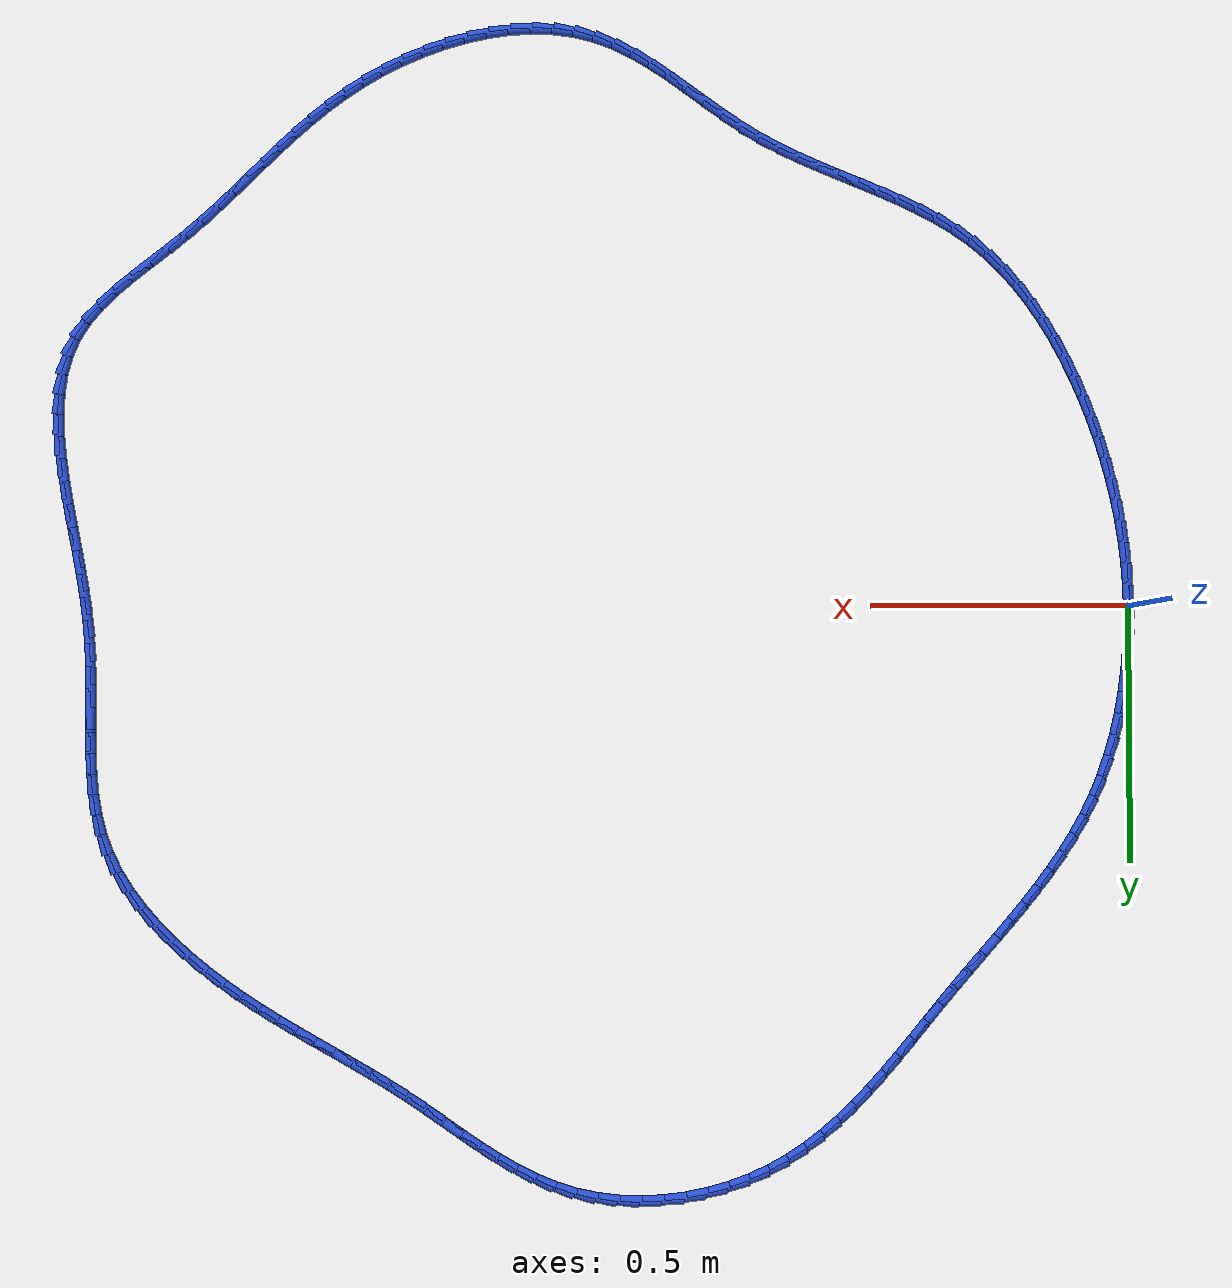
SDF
<sdf version="1.6">
 <world name="default">
  <light name="sun" type="directional">
   <pose>0 0 10 0 -0 0</pose>
   <diffuse>0.8 0.8 0.8 1</diffuse>
   <specular>0.2 0.2 0.2 1</specular>
   <attenuation>
    <range>1000</range>
    <constant>0.9</constant>
    <linear>0.01</linear>
    <quadratic>0.001</quadratic>
   </attenuation>
   <direction>-0.5 0.1 -0.9</direction>
  </light>
  <model name="ground_plane">
   <static>1</static>
   <link name="link">
    <collision name="collision">
     <geometry><plane><normal>0 0 1</normal><size>100 100</size></plane></geometry>
     <surface><friction><ode><mu>100</mu><mu2>50</mu2></ode></friction></surface>
    </collision>
    <visual name="visual">
     <cast_shadows>0</cast_shadows>
     <geometry><plane><normal>0 0 1</normal><size>100 100</size></plane></geometry>
     <material>
      <script><uri>file://media/materials/scripts/gazebo.material</uri><name>Gazebo/WhiteGlow</name></script>
     </material>
    </visual>
   </link>
  </model>
  <gravity>0 0 -9.8</gravity>
  <magnetic_field>6e-06 2.3e-05 -4.2e-05</magnetic_field>
  <atmosphere type="adiabatic"/>
  <physics name="default_physics" default="0" type="ode">
   <max_step_size>0.001</max_step_size>
   <real_time_factor>1</real_time_factor>
   <real_time_update_rate>1000</real_time_update_rate>
  </physics>
  <scene><ambient>0.4 0.4 0.4 1</ambient><background>0.7 0.7 0.7 1</background><shadows>1</shadows></scene>
  <spherical_coordinates>
   <surface_model>EARTH_WGS84</surface_model>
   <latitude_deg>0</latitude_deg>
   <longitude_deg>0</longitude_deg>
   <elevation>0</elevation>
   <heading_deg>0</heading_deg>
  </spherical_coordinates>
  <model name="line">
   <link name="link_0">
    <pose>8.673617379884035e-19 -9.71445146547012e-17 0.01 0 1.57 1.564009834167707</pose>
    <collision name="collision">
     <geometry><cylinder><radius>0.01</radius><length>0.08</length></cylinder></geometry>
    </collision>
    <visual name="visual">
     <material>
      <script><name>Gazebo/Blue</name><uri>file://media/materials/scripts/gazebo.material</uri></script>
     </material>
     <geometry><cylinder><radius>0.01</radius><length>0.08</length></cylinder></geometry>
    </visual>
   </link>
   <link name="link_1">
    <pose>0.00028746095920389667 0.04235715882042236 0.01 0 1.57 1.522763177604085</pose>
    <collision name="collision">
     <geometry><cylinder><radius>0.01</radius><length>0.08</length></cylinder></geometry>
    </collision>
    <visual name="visual">
     <material>
      <script><name>Gazebo/Blue</name><uri>file://media/materials/scripts/gazebo.material</uri></script>
     </material>
     <geometry><cylinder><radius>0.01</radius><length>0.08</length></cylinder></geometry>
    </visual>
   </link>
   <link name="link_2">
    <pose>0.0023284698408756674 0.0848161483708669 0.01 0 1.57 1.4801706708943538</pose>
    <collision name="collision">
     <geometry><cylinder><radius>0.01</radius><length>0.08</length></cylinder></geometry>
    </collision>
    <visual name="visual">
     <material>
      <script><name>Gazebo/Blue</name><uri>file://media/materials/scripts/gazebo.material</uri></script>
     </material>
     <geometry><cylinder><radius>0.01</radius><length>0.08</length></cylinder></geometry>
    </visual>
   </link>
   <link name="link_3">
    <pose>0.00618078458582902 0.1272077047341136 0.01 0 1.57 1.4358977339599144</pose>
    <collision name="collision">
     <geometry><cylinder><radius>0.01</radius><length>0.08</length></cylinder></geometry>
    </collision>
    <visual name="visual">
     <material>
      <script><name>Gazebo/Blue</name><uri>file://media/materials/scripts/gazebo.material</uri></script>
     </material>
     <geometry><cylinder><radius>0.01</radius><length>0.08</length></cylinder></geometry>
    </visual>
   </link>
   <link name="link_4">
    <pose>0.011902163134877644 0.1693625639929425 0.01 0 1.57 1.3896101384911503</pose>
    <collision name="collision">
     <geometry><cylinder><radius>0.01</radius><length>0.08</length></cylinder></geometry>
    </collision>
    <visual name="visual">
     <material>
      <script><name>Gazebo/Blue</name><uri>file://media/materials/scripts/gazebo.material</uri></script>
     </material>
     <geometry><cylinder><radius>0.01</radius><length>0.08</length></cylinder></geometry>
    </visual>
   </link>
   <link name="link_5">
    <pose>0.019550363428835253 0.2111114622301337 0.01 0 1.57 1.3409750623026198</pose>
    <collision name="collision">
     <geometry><cylinder><radius>0.01</radius><length>0.08</length></cylinder></geometry>
    </collision>
    <visual name="visual">
     <material>
      <script><name>Gazebo/Blue</name><uri>file://media/materials/scripts/gazebo.material</uri></script>
     </material>
     <geometry><cylinder><radius>0.01</radius><length>0.08</length></cylinder></geometry>
    </visual>
   </link>
   <link name="link_6">
    <pose>0.029183143408515556 0.2522851355284672 0.01 0 1.57 1.2896651377609418</pose>
    <collision name="collision">
     <geometry><cylinder><radius>0.01</radius><length>0.08</length></cylinder></geometry>
    </collision>
    <visual name="visual">
     <material>
      <script><name>Gazebo/Blue</name><uri>file://media/materials/scripts/gazebo.material</uri></script>
     </material>
     <geometry><cylinder><radius>0.01</radius><length>0.08</length></cylinder></geometry>
    </visual>
   </link>
   <link name="link_7">
    <pose>0.04085826101473224 0.29271431997072317 0.01 0 1.57 1.2353662507474885</pose>
    <collision name="collision">
     <geometry><cylinder><radius>0.01</radius><length>0.08</length></cylinder></geometry>
    </collision>
    <visual name="visual">
     <material>
      <script><name>Gazebo/Blue</name><uri>file://media/materials/scripts/gazebo.material</uri></script>
     </material>
     <geometry><cylinder><radius>0.01</radius><length>0.08</length></cylinder></geometry>
    </visual>
   </link>
   <link name="link_8">
    <pose>0.054633474188298996 0.33222975163968144 0.01 0 1.57 1.1777899274220252</pose>
    <collision name="collision">
     <geometry><cylinder><radius>0.01</radius><length>0.08</length></cylinder></geometry>
    </collision>
    <visual name="visual">
     <material>
      <script><name>Gazebo/Blue</name><uri>file://media/materials/scripts/gazebo.material</uri></script>
     </material>
     <geometry><cylinder><radius>0.01</radius><length>0.08</length></cylinder></geometry>
    </visual>
   </link>
   <link name="link_9">
    <pose>0.07056654087002955 0.37066216661812235 0.01 0 1.57 1.1172198005887168</pose>
    <collision name="collision">
     <geometry><cylinder><radius>0.01</radius><length>0.08</length></cylinder></geometry>
    </collision>
    <visual name="visual">
     <material>
      <script><name>Gazebo/Blue</name><uri>file://media/materials/scripts/gazebo.material</uri></script>
     </material>
     <geometry><cylinder><radius>0.01</radius><length>0.08</length></cylinder></geometry>
    </visual>
   </link>
   <link name="link_10">
    <pose>0.0886993675038916 0.40785970762088225 0.01 0 1.57 1.059518374034115</pose>
    <collision name="collision">
     <geometry><cylinder><radius>0.01</radius><length>0.08</length></cylinder></geometry>
    </collision>
    <visual name="visual">
     <material>
      <script><name>Gazebo/Blue</name><uri>file://media/materials/scripts/gazebo.material</uri></script>
     </material>
     <geometry><cylinder><radius>0.01</radius><length>0.08</length></cylinder></geometry>
    </visual>
   </link>
   <link name="link_11">
    <pose>0.10889857330115774 0.44386300141609336 0.01 0 1.57 1.0087617799985393</pose>
    <collision name="collision">
     <geometry><cylinder><radius>0.01</radius><length>0.08</length></cylinder></geometry>
    </collision>
    <visual name="visual">
     <material>
      <script><name>Gazebo/Blue</name><uri>file://media/materials/scripts/gazebo.material</uri></script>
     </material>
     <geometry><cylinder><radius>0.01</radius><length>0.08</length></cylinder></geometry>
    </visual>
   </link>
   <link name="link_12">
    <pose>0.13092181477432416 0.47883232742197535 0.01 0 1.57 0.9653036912971279</pose>
    <collision name="collision">
     <geometry><cylinder><radius>0.01</radius><length>0.08</length></cylinder></geometry>
    </collision>
    <visual name="visual">
     <material>
      <script><name>Gazebo/Blue</name><uri>file://media/materials/scripts/gazebo.material</uri></script>
     </material>
     <geometry><cylinder><radius>0.01</radius><length>0.08</length></cylinder></geometry>
    </visual>
   </link>
   <link name="link_13">
    <pose>0.1545251090706547 0.5129297652544 0.01 0 1.57 0.9292409537150683</pose>
    <collision name="collision">
     <geometry><cylinder><radius>0.01</radius><length>0.08</length></cylinder></geometry>
    </collision>
    <visual name="visual">
     <material>
      <script><name>Gazebo/Blue</name><uri>file://media/materials/scripts/gazebo.material</uri></script>
     </material>
     <geometry><cylinder><radius>0.01</radius><length>0.08</length></cylinder></geometry>
    </visual>
   </link>
   <link name="link_14">
    <pose>0.17946447333741347 0.5463173945292396 0.01 0 1.57 0.9005362752324886</pose>
    <collision name="collision">
     <geometry><cylinder><radius>0.01</radius><length>0.08</length></cylinder></geometry>
    </collision>
    <visual name="visual">
     <material>
      <script><name>Gazebo/Blue</name><uri>file://media/materials/scripts/gazebo.material</uri></script>
     </material>
     <geometry><cylinder><radius>0.01</radius><length>0.08</length></cylinder></geometry>
    </visual>
   </link>
   <link name="link_15">
    <pose>0.20549592472186418 0.5791572948623656 0.01 0 1.57 0.8790779466856905</pose>
    <collision name="collision">
     <geometry><cylinder><radius>0.01</radius><length>0.08</length></cylinder></geometry>
    </collision>
    <visual name="visual">
     <material>
      <script><name>Gazebo/Blue</name><uri>file://media/materials/scripts/gazebo.material</uri></script>
     </material>
     <geometry><cylinder><radius>0.01</radius><length>0.08</length></cylinder></geometry>
    </visual>
   </link>
   <link name="link_16">
    <pose>0.2323754803712709 0.6116115458696497 0.01 0 1.57 0.8647265287988759</pose>
    <collision name="collision">
     <geometry><cylinder><radius>0.01</radius><length>0.08</length></cylinder></geometry>
    </collision>
    <visual name="visual">
     <material>
      <script><name>Gazebo/Blue</name><uri>file://media/materials/scripts/gazebo.material</uri></script>
     </material>
     <geometry><cylinder><radius>0.01</radius><length>0.08</length></cylinder></geometry>
    </visual>
   </link>
   <link name="link_17">
    <pose>0.2598591574328976 0.6438422271669644 0.01 0 1.57 0.8573477198979467</pose>
    <collision name="collision">
     <geometry><cylinder><radius>0.01</radius><length>0.08</length></cylinder></geometry>
    </collision>
    <visual name="visual">
     <material>
      <script><name>Gazebo/Blue</name><uri>file://media/materials/scripts/gazebo.material</uri></script>
     </material>
     <geometry><cylinder><radius>0.01</radius><length>0.08</length></cylinder></geometry>
    </visual>
   </link>
   <link name="link_18">
    <pose>0.28770297305400805 0.676011418370181 0.01 0 1.57 0.8568325617086788</pose>
    <collision name="collision">
     <geometry><cylinder><radius>0.01</radius><length>0.08</length></cylinder></geometry>
    </collision>
    <visual name="visual">
     <material>
      <script><name>Gazebo/Blue</name><uri>file://media/materials/scripts/gazebo.material</uri></script>
     </material>
     <geometry><cylinder><radius>0.01</radius><length>0.08</length></cylinder></geometry>
    </visual>
   </link>
   <link name="link_19">
    <pose>0.3156629443818662 0.7082811990951715 0.01 0 1.57 0.8631066420745012</pose>
    <collision name="collision">
     <geometry><cylinder><radius>0.01</radius><length>0.08</length></cylinder></geometry>
    </collision>
    <visual name="visual">
     <material>
      <script><name>Gazebo/Blue</name><uri>file://media/materials/scripts/gazebo.material</uri></script>
     </material>
     <geometry><cylinder><radius>0.01</radius><length>0.08</length></cylinder></geometry>
    </visual>
   </link>
   <link name="link_20">
    <pose>0.34349508856373623 0.7408136489578082 0.01 0 1.57 0.8751013430125898</pose>
    <collision name="collision">
     <geometry><cylinder><radius>0.01</radius><length>0.08</length></cylinder></geometry>
    </collision>
    <visual name="visual">
     <material>
      <script><name>Gazebo/Blue</name><uri>file://media/materials/scripts/gazebo.material</uri></script>
     </material>
     <geometry><cylinder><radius>0.01</radius><length>0.08</length></cylinder></geometry>
    </visual>
   </link>
   <link name="link_21">
    <pose>0.37098738198274256 0.773740297546031 0.01 0 1.57 0.8837434149172014</pose>
    <collision name="collision">
     <geometry><cylinder><radius>0.01</radius><length>0.08</length></cylinder></geometry>
    </collision>
    <visual name="visual">
     <material>
      <script><name>Gazebo/Blue</name><uri>file://media/materials/scripts/gazebo.material</uri></script>
     </material>
     <geometry><cylinder><radius>0.01</radius><length>0.08</length></cylinder></geometry>
    </visual>
   </link>
   <link name="link_22">
    <pose>0.3982101062944335 0.8069228171209297 0.01 0 1.57 0.884342227536992</pose>
    <collision name="collision">
     <geometry><cylinder><radius>0.01</radius><length>0.08</length></cylinder></geometry>
    </collision>
    <visual name="visual">
     <material>
      <script><name>Gazebo/Blue</name><uri>file://media/materials/scripts/gazebo.material</uri></script>
     </material>
     <geometry><cylinder><radius>0.01</radius><length>0.08</length></cylinder></geometry>
    </visual>
   </link>
   <link name="link_23">
    <pose>0.425380674754983 0.8400822359517205 0.01 0 1.57 0.87683117857295</pose>
    <collision name="collision">
     <geometry><cylinder><radius>0.01</radius><length>0.08</length></cylinder></geometry>
    </collision>
    <visual name="visual">
     <material>
      <script><name>Gazebo/Blue</name><uri>file://media/materials/scripts/gazebo.material</uri></script>
     </material>
     <geometry><cylinder><radius>0.01</radius><length>0.08</length></cylinder></geometry>
    </visual>
   </link>
   <link name="link_24">
    <pose>0.45271777054567386 0.872938368378484 0.01 0 1.57 0.861098824956909</pose>
    <collision name="collision">
     <geometry><cylinder><radius>0.01</radius><length>0.08</length></cylinder></geometry>
    </collision>
    <visual name="visual">
     <material>
      <script><name>Gazebo/Blue</name><uri>file://media/materials/scripts/gazebo.material</uri></script>
     </material>
     <geometry><cylinder><radius>0.01</radius><length>0.08</length></cylinder></geometry>
    </visual>
   </link>
   <link name="link_25">
    <pose>0.4804400768477891 0.9052110287413015 0.01 0 1.57 0.8369602239063719</pose>
    <collision name="collision">
     <geometry><cylinder><radius>0.01</radius><length>0.08</length></cylinder></geometry>
    </collision>
    <visual name="visual">
     <material>
      <script><name>Gazebo/Blue</name><uri>file://media/materials/scripts/gazebo.material</uri></script>
     </material>
     <geometry><cylinder><radius>0.01</radius><length>0.08</length></cylinder></geometry>
    </visual>
   </link>
   <link name="link_26">
    <pose>0.508766276842612 0.9366200313802546 0.01 0 1.57 0.8041858604167499</pose>
    <collision name="collision">
     <geometry><cylinder><radius>0.01</radius><length>0.08</length></cylinder></geometry>
    </collision>
    <visual name="visual">
     <material>
      <script><name>Gazebo/Blue</name><uri>file://media/materials/scripts/gazebo.material</uri></script>
     </material>
     <geometry><cylinder><radius>0.01</radius><length>0.08</length></cylinder></geometry>
    </visual>
   </link>
   <link name="link_27">
    <pose>0.5379150537114253 0.9668851906354239 0.01 0 1.57 0.7625513848017142</pose>
    <collision name="collision">
     <geometry><cylinder><radius>0.01</radius><length>0.08</length></cylinder></geometry>
    </collision>
    <visual name="visual">
     <material>
      <script><name>Gazebo/Blue</name><uri>file://media/materials/scripts/gazebo.material</uri></script>
     </material>
     <geometry><cylinder><radius>0.01</radius><length>0.08</length></cylinder></geometry>
    </visual>
   </link>
   <link name="link_28">
    <pose>0.5681050906355118 0.9957263208468906 0.01 0 1.57 0.7119124789078913</pose>
    <collision name="collision">
     <geometry><cylinder><radius>0.01</radius><length>0.08</length></cylinder></geometry>
    </collision>
    <visual name="visual">
     <material>
      <script><name>Gazebo/Blue</name><uri>file://media/materials/scripts/gazebo.material</uri></script>
     </material>
     <geometry><cylinder><radius>0.01</radius><length>0.08</length></cylinder></geometry>
    </visual>
   </link>
   <link name="link_29">
    <pose>0.5995550707961551 1.0228632363547359 0.01 0 1.57 0.6523063235169997</pose>
    <collision name="collision">
     <geometry><cylinder><radius>0.01</radius><length>0.08</length></cylinder></geometry>
    </collision>
    <visual name="visual">
     <material>
      <script><name>Gazebo/Blue</name><uri>file://media/materials/scripts/gazebo.material</uri></script>
     </material>
     <geometry><cylinder><radius>0.01</radius><length>0.08</length></cylinder></geometry>
    </visual>
   </link>
   <link name="link_30">
    <pose>0.6324836773746376 1.048015751499041 0.01 0 1.57 0.5840732497624731</pose>
    <collision name="collision">
     <geometry><cylinder><radius>0.01</radius><length>0.08</length></cylinder></geometry>
    </collision>
    <visual name="visual">
     <material>
      <script><name>Gazebo/Blue</name><uri>file://media/materials/scripts/gazebo.material</uri></script>
     </material>
     <geometry><cylinder><radius>0.01</radius><length>0.08</length></cylinder></geometry>
    </visual>
   </link>
   <link name="link_31">
    <pose>0.6671095935522425 1.0709036806198868 0.01 0 1.57 0.5079787694916206</pose>
    <collision name="collision">
     <geometry><cylinder><radius>0.01</radius><length>0.08</length></cylinder></geometry>
    </collision>
    <visual name="visual">
     <material>
      <script><name>Gazebo/Blue</name><uri>file://media/materials/scripts/gazebo.material</uri></script>
     </material>
     <geometry><cylinder><radius>0.01</radius><length>0.08</length></cylinder></geometry>
    </visual>
   </link>
   <link name="link_32">
    <pose>0.7036514808377259 1.0912468442134728 0.01 0 1.57 0.42721877108998774</pose>
    <collision name="collision">
     <geometry><cylinder><radius>0.01</radius><length>0.08</length></cylinder></geometry>
    </collision>
    <visual name="visual">
     <material>
      <script><name>Gazebo/Blue</name><uri>file://media/materials/scripts/gazebo.material</uri></script>
     </material>
     <geometry><cylinder><radius>0.01</radius><length>0.08</length></cylinder></geometry>
    </visual>
   </link>
   <link name="link_33">
    <pose>0.7422067815416707 1.10879949529804 0.01 0 1.57 0.34858312195354996</pose>
    <collision name="collision">
     <geometry><cylinder><radius>0.01</radius><length>0.08</length></cylinder></geometry>
    </collision>
    <visual name="visual">
     <material>
      <script><name>Gazebo/Blue</name><uri>file://media/materials/scripts/gazebo.material</uri></script>
     </material>
     <geometry><cylinder><radius>0.01</radius><length>0.08</length></cylinder></geometry>
    </visual>
   </link>
   <link name="link_34">
    <pose>0.7824672831377649 1.1234311138469864 0.01 0 1.57 0.27220053162975905</pose>
    <collision name="collision">
     <geometry><cylinder><radius>0.01</radius><length>0.08</length></cylinder></geometry>
    </collision>
    <visual name="visual">
     <material>
      <script><name>Gazebo/Blue</name><uri>file://media/materials/scripts/gazebo.material</uri></script>
     </material>
     <geometry><cylinder><radius>0.01</radius><length>0.08</length></cylinder></geometry>
    </visual>
   </link>
   <link name="link_35">
    <pose>0.8240400159422563 1.1350352552502754 0.01 0 1.57 0.1967578196151451</pose>
    <collision name="collision">
     <geometry><cylinder><radius>0.01</radius><length>0.08</length></cylinder></geometry>
    </collision>
    <visual name="visual">
     <material>
      <script><name>Gazebo/Blue</name><uri>file://media/materials/scripts/gazebo.material</uri></script>
     </material>
     <geometry><cylinder><radius>0.01</radius><length>0.08</length></cylinder></geometry>
    </visual>
   </link>
   <link name="link_36">
    <pose>0.8665320102713926 1.1435054748978712 0.01 0 1.57 0.12097910452303008</pose>
    <collision name="collision">
     <geometry><cylinder><radius>0.01</radius><length>0.08</length></cylinder></geometry>
    </collision>
    <visual name="visual">
     <material>
      <script><name>Gazebo/Blue</name><uri>file://media/materials/scripts/gazebo.material</uri></script>
     </material>
     <geometry><cylinder><radius>0.01</radius><length>0.08</length></cylinder></geometry>
    </visual>
   </link>
   <link name="link_37">
    <pose>0.9095502964414214 1.148735328179737 0.01 0 1.57 0.04361015673929334</pose>
    <collision name="collision">
     <geometry><cylinder><radius>0.01</radius><length>0.08</length></cylinder></geometry>
    </collision>
    <visual name="visual">
     <material>
      <script><name>Gazebo/Blue</name><uri>file://media/materials/scripts/gazebo.material</uri></script>
     </material>
     <geometry><cylinder><radius>0.01</radius><length>0.08</length></cylinder></geometry>
    </visual>
   </link>
   <link name="link_38">
    <pose>0.9527019047685901 1.1506183704858357 0.01 0 1.57 -0.03659222740040497</pose>
    <collision name="collision">
     <geometry><cylinder><radius>0.01</radius><length>0.08</length></cylinder></geometry>
    </collision>
    <visual name="visual">
     <material>
      <script><name>Gazebo/Blue</name><uri>file://media/materials/scripts/gazebo.material</uri></script>
     </material>
     <geometry><cylinder><radius>0.01</radius><length>0.08</length></cylinder></geometry>
    </visual>
   </link>
   <link name="link_39">
    <pose>0.9955938655691466 1.1490481572061317 0.01 0 1.57 -0.12085681771139328</pose>
    <collision name="collision">
     <geometry><cylinder><radius>0.01</radius><length>0.08</length></cylinder></geometry>
    </collision>
    <visual name="visual">
     <material>
      <script><name>Gazebo/Blue</name><uri>file://media/materials/scripts/gazebo.material</uri></script>
     </material>
     <geometry><cylinder><radius>0.01</radius><length>0.08</length></cylinder></geometry>
    </visual>
   </link>
   <link name="link_40">
    <pose>1.037833209159338 1.143918243730588 0.01 0 1.57 -0.21036964972758848</pose>
    <collision name="collision">
     <geometry><cylinder><radius>0.01</radius><length>0.08</length></cylinder></geometry>
    </collision>
    <visual name="visual">
     <material>
      <script><name>Gazebo/Blue</name><uri>file://media/materials/scripts/gazebo.material</uri></script>
     </material>
     <geometry><cylinder><radius>0.01</radius><length>0.08</length></cylinder></geometry>
    </visual>
   </link>
   <link name="link_41">
    <pose>1.0790269658554126 1.1351221854491675 0.01 0 1.57 -0.3051452091076937</pose>
    <collision name="collision">
     <geometry><cylinder><radius>0.01</radius><length>0.08</length></cylinder></geometry>
    </collision>
    <visual name="visual">
     <material>
      <script><name>Gazebo/Blue</name><uri>file://media/materials/scripts/gazebo.material</uri></script>
     </material>
     <geometry><cylinder><radius>0.01</radius><length>0.08</length></cylinder></geometry>
    </visual>
   </link>
   <link name="link_42">
    <pose>1.1188149187416796 1.122589663245133 0.01 0 1.57 -0.39360961031222264</pose>
    <collision name="collision">
     <geometry><cylinder><radius>0.01</radius><length>0.08</length></cylinder></geometry>
    </collision>
    <visual name="visual">
     <material>
      <script><name>Gazebo/Blue</name><uri>file://media/materials/scripts/gazebo.material</uri></script>
     </material>
     <geometry><cylinder><radius>0.01</radius><length>0.08</length></cylinder></geometry>
    </visual>
   </link>
   <link name="link_43">
    <pose>1.157198799114459 1.1066495779297358 0.01 0 1.57 -0.46724245987568186</pose>
    <collision name="collision">
     <geometry><cylinder><radius>0.01</radius><length>0.08</length></cylinder></geometry>
    </collision>
    <visual name="visual">
     <material>
      <script><name>Gazebo/Blue</name><uri>file://media/materials/scripts/gazebo.material</uri></script>
     </material>
     <geometry><cylinder><radius>0.01</radius><length>0.08</length></cylinder></geometry>
    </visual>
   </link>
   <link name="link_44">
    <pose>1.1944052243499788 1.08787887409963 0.01 0 1.57 -0.5253866980923065</pose>
    <collision name="collision">
     <geometry><cylinder><radius>0.01</radius><length>0.08</length></cylinder></geometry>
    </collision>
    <visual name="visual">
     <material>
      <script><name>Gazebo/Blue</name><uri>file://media/materials/scripts/gazebo.material</uri></script>
     </material>
     <geometry><cylinder><radius>0.01</radius><length>0.08</length></cylinder></geometry>
    </visual>
   </link>
   <link name="link_45">
    <pose>1.2306641906466071 1.0668582231087451 0.01 0 1.57 -0.5681819087192342</pose>
    <collision name="collision">
     <geometry><cylinder><radius>0.01</radius><length>0.08</length></cylinder></geometry>
    </collision>
    <visual name="visual">
     <material>
      <script><name>Gazebo/Blue</name><uri>file://media/materials/scripts/gazebo.material</uri></script>
     </material>
     <geometry><cylinder><radius>0.01</radius><length>0.08</length></cylinder></geometry>
    </visual>
   </link>
   <link name="link_46">
    <pose>1.2662056942027142 1.04416829631101 0.01 0 1.57 -0.5960401882315445</pose>
    <collision name="collision">
     <geometry><cylinder><radius>0.01</radius><length>0.08</length></cylinder></geometry>
    </collision>
    <visual name="visual">
     <material>
      <script><name>Gazebo/Blue</name><uri>file://media/materials/scripts/gazebo.material</uri></script>
     </material>
     <geometry><cylinder><radius>0.01</radius><length>0.08</length></cylinder></geometry>
    </visual>
   </link>
   <link name="link_47">
    <pose>1.301259731216669 1.0203897650603542 0.01 0 1.57 -0.6093526773493374</pose>
    <collision name="collision">
     <geometry><cylinder><radius>0.01</radius><length>0.08</length></cylinder></geometry>
    </collision>
    <visual name="visual">
     <material>
      <script><name>Gazebo/Blue</name><uri>file://media/materials/scripts/gazebo.material</uri></script>
     </material>
     <geometry><cylinder><radius>0.01</radius><length>0.08</length></cylinder></geometry>
    </visual>
   </link>
   <link name="link_48">
    <pose>1.3360562978868402 0.996103300710706 0.01 0 1.57 -0.6083160347230925</pose>
    <collision name="collision">
     <geometry><cylinder><radius>0.01</radius><length>0.08</length></cylinder></geometry>
    </collision>
    <visual name="visual">
     <material>
      <script><name>Gazebo/Blue</name><uri>file://media/materials/scripts/gazebo.material</uri></script>
     </material>
     <geometry><cylinder><radius>0.01</radius><length>0.08</length></cylinder></geometry>
    </visual>
   </link>
   <link name="link_49">
    <pose>1.370825390411598 0.9718895746159956 0.01 0 1.57 -0.5928570110164331</pose>
    <collision name="collision">
     <geometry><cylinder><radius>0.01</radius><length>0.08</length></cylinder></geometry>
    </collision>
    <visual name="visual">
     <material>
      <script><name>Gazebo/Blue</name><uri>file://media/materials/scripts/gazebo.material</uri></script>
     </material>
     <geometry><cylinder><radius>0.01</radius><length>0.08</length></cylinder></geometry>
    </visual>
   </link>
   <link name="link_50">
    <pose>1.4057969723211037 0.9483291705678364 0.01 0 1.57 -0.5671825561247898</pose>
    <collision name="collision">
     <geometry><cylinder><radius>0.01</radius><length>0.08</length></cylinder></geometry>
    </collision>
    <visual name="visual">
     <material>
      <script><name>Gazebo/Blue</name><uri>file://media/materials/scripts/gazebo.material</uri></script>
     </material>
     <geometry><cylinder><radius>0.01</radius><length>0.08</length></cylinder></geometry>
    </visual>
   </link>
   <link name="link_51">
    <pose>1.4411329112186873 0.9258201512635085 0.01 0 1.57 -0.5452758185804613</pose>
    <collision name="collision">
     <geometry><cylinder><radius>0.01</radius><length>0.08</length></cylinder></geometry>
    </collision>
    <visual name="visual">
     <material>
      <script><name>Gazebo/Blue</name><uri>file://media/materials/scripts/gazebo.material</uri></script>
     </material>
     <geometry><cylinder><radius>0.01</radius><length>0.08</length></cylinder></geometry>
    </visual>
   </link>
   <link name="link_52">
    <pose>1.47678355045517 0.9041936198207343 0.01 0 1.57 -0.5300640518500292</pose>
    <collision name="collision">
     <geometry><cylinder><radius>0.01</radius><length>0.08</length></cylinder></geometry>
    </collision>
    <visual name="visual">
     <material>
      <script><name>Gazebo/Blue</name><uri>file://media/materials/scripts/gazebo.material</uri></script>
     </material>
     <geometry><cylinder><radius>0.01</radius><length>0.08</length></cylinder></geometry>
    </visual>
   </link>
   <link name="link_53">
    <pose>1.5126582826934436 0.8831709170744877 0.01 0 1.57 -0.5216841611636733</pose>
    <collision name="collision">
     <geometry><cylinder><radius>0.01</radius><length>0.08</length></cylinder></geometry>
    </collision>
    <visual name="visual">
     <material>
      <script><name>Gazebo/Blue</name><uri>file://media/materials/scripts/gazebo.material</uri></script>
     </material>
     <geometry><cylinder><radius>0.01</radius><length>0.08</length></cylinder></geometry>
    </visual>
   </link>
   <link name="link_54">
    <pose>1.548666500596397 0.8624733838597424 0.01 0 1.57 -0.5201992938097166</pose>
    <collision name="collision">
     <geometry><cylinder><radius>0.01</radius><length>0.08</length></cylinder></geometry>
    </collision>
    <visual name="visual">
     <material>
      <script><name>Gazebo/Blue</name><uri>file://media/materials/scripts/gazebo.material</uri></script>
     </material>
     <geometry><cylinder><radius>0.01</radius><length>0.08</length></cylinder></geometry>
    </visual>
   </link>
   <link name="link_55">
    <pose>1.5847175968269216 0.841822361011473 0.01 0 1.57 -0.5256091212722444</pose>
    <collision name="collision">
     <geometry><cylinder><radius>0.01</radius><length>0.08</length></cylinder></geometry>
    </collision>
    <visual name="visual">
     <material>
      <script><name>Gazebo/Blue</name><uri>file://media/materials/scripts/gazebo.material</uri></script>
     </material>
     <geometry><cylinder><radius>0.01</radius><length>0.08</length></cylinder></geometry>
    </visual>
   </link>
   <link name="link_56">
    <pose>1.620720964047909 0.8209391893646535 0.01 0 1.57 -0.5378520465299659</pose>
    <collision name="collision">
     <geometry><cylinder><radius>0.01</radius><length>0.08</length></cylinder></geometry>
    </collision>
    <visual name="visual">
     <material>
      <script><name>Gazebo/Blue</name><uri>file://media/materials/scripts/gazebo.material</uri></script>
     </material>
     <geometry><cylinder><radius>0.01</radius><length>0.08</length></cylinder></geometry>
    </visual>
   </link>
   <link name="link_57">
    <pose>1.656585994922247 0.7995452097542576 0.01 0 1.57 -0.556799187580998</pose>
    <collision name="collision">
     <geometry><cylinder><radius>0.01</radius><length>0.08</length></cylinder></geometry>
    </collision>
    <visual name="visual">
     <material>
      <script><name>Gazebo/Blue</name><uri>file://media/materials/scripts/gazebo.material</uri></script>
     </material>
     <geometry><cylinder><radius>0.01</radius><length>0.08</length></cylinder></geometry>
    </visual>
   </link>
   <link name="link_58">
    <pose>1.6922220821128289 0.77736176301526 0.01 0 1.57 -0.5822411889681539</pose>
    <collision name="collision">
     <geometry><cylinder><radius>0.01</radius><length>0.08</length></cylinder></geometry>
    </collision>
    <visual name="visual">
     <material>
      <script><name>Gazebo/Blue</name><uri>file://media/materials/scripts/gazebo.material</uri></script>
     </material>
     <geometry><cylinder><radius>0.01</radius><length>0.08</length></cylinder></geometry>
    </visual>
   </link>
   <link name="link_59">
    <pose>1.7275386182825438 0.7541101899826348 0.01 0 1.57 -0.6138701900718513</pose>
    <collision name="collision">
     <geometry><cylinder><radius>0.01</radius><length>0.08</length></cylinder></geometry>
    </collision>
    <visual name="visual">
     <material>
      <script><name>Gazebo/Blue</name><uri>file://media/materials/scripts/gazebo.material</uri></script>
     </material>
     <geometry><cylinder><radius>0.01</radius><length>0.08</length></cylinder></geometry>
    </visual>
   </link>
   <link name="link_60">
    <pose>1.7624449960942832 0.7295118314913559 0.01 0 1.57 -0.6512013186573202</pose>
    <collision name="collision">
     <geometry><cylinder><radius>0.01</radius><length>0.08</length></cylinder></geometry>
    </collision>
    <visual name="visual">
     <material>
      <script><name>Gazebo/Blue</name><uri>file://media/materials/scripts/gazebo.material</uri></script>
     </material>
     <geometry><cylinder><radius>0.01</radius><length>0.08</length></cylinder></geometry>
    </visual>
   </link>
   <link name="link_61">
    <pose>1.7968209020543795 0.7033138949016474 0.01 0 1.57 -0.6936236331819965</pose>
    <collision name="collision">
     <geometry><cylinder><radius>0.01</radius><length>0.08</length></cylinder></geometry>
    </collision>
    <visual name="visual">
     <material>
      <script><name>Gazebo/Blue</name><uri>file://media/materials/scripts/gazebo.material</uri></script>
     </material>
     <geometry><cylinder><radius>0.01</radius><length>0.08</length></cylinder></geometry>
    </visual>
   </link>
   <link name="link_62">
    <pose>1.830299769531715 0.6754780115765598 0.01 0 1.57 -0.7417293635034974</pose>
    <collision name="collision">
     <geometry><cylinder><radius>0.01</radius><length>0.08</length></cylinder></geometry>
    </collision>
    <visual name="visual">
     <material>
      <script><name>Gazebo/Blue</name><uri>file://media/materials/scripts/gazebo.material</uri></script>
     </material>
     <geometry><cylinder><radius>0.01</radius><length>0.08</length></cylinder></geometry>
    </visual>
   </link>
   <link name="link_63">
    <pose>1.8623932691809577 0.6460718373093204 0.01 0 1.57 -0.7966712455004558</pose>
    <collision name="collision">
     <geometry><cylinder><radius>0.01</radius><length>0.08</length></cylinder></geometry>
    </collision>
    <visual name="visual">
     <material>
      <script><name>Gazebo/Blue</name><uri>file://media/materials/scripts/gazebo.material</uri></script>
     </material>
     <geometry><cylinder><radius>0.01</radius><length>0.08</length></cylinder></geometry>
    </visual>
   </link>
   <link name="link_64">
    <pose>1.892612206219793 0.615163781469184 0.01 0 1.57 -0.8597887696904641</pose>
    <collision name="collision">
     <geometry><cylinder><radius>0.01</radius><length>0.08</length></cylinder></geometry>
    </collision>
    <visual name="visual">
     <material>
      <script><name>Gazebo/Blue</name><uri>file://media/materials/scripts/gazebo.material</uri></script>
     </material>
     <geometry><cylinder><radius>0.01</radius><length>0.08</length></cylinder></geometry>
    </visual>
   </link>
   <link name="link_65">
    <pose>1.9204673858659103 0.582822253425406 0.01 0 1.57 -0.9325892000217171</pose>
    <collision name="collision">
     <geometry><cylinder><radius>0.01</radius><length>0.08</length></cylinder></geometry>
    </collision>
    <visual name="visual">
     <material>
      <script><name>Gazebo/Blue</name><uri>file://media/materials/scripts/gazebo.material</uri></script>
     </material>
     <geometry><cylinder><radius>0.01</radius><length>0.08</length></cylinder></geometry>
    </visual>
   </link>
   <link name="link_66">
    <pose>1.9454696133369975 0.549115662547241 0.01 0 1.57 -1.0166663605380593</pose>
    <collision name="collision">
     <geometry><cylinder><radius>0.01</radius><length>0.08</length></cylinder></geometry>
    </collision>
    <visual name="visual">
     <material>
      <script><name>Gazebo/Blue</name><uri>file://media/materials/scripts/gazebo.material</uri></script>
     </material>
     <geometry><cylinder><radius>0.01</radius><length>0.08</length></cylinder></geometry>
    </visual>
   </link>
   <link name="link_67">
    <pose>1.9671296938507412 0.5141124182039443 0.01 0 1.57 -1.113505925142746</pose>
    <collision name="collision">
     <geometry><cylinder><radius>0.01</radius><length>0.08</length></cylinder></geometry>
    </collision>
    <visual name="visual">
     <material>
      <script><name>Gazebo/Blue</name><uri>file://media/materials/scripts/gazebo.material</uri></script>
     </material>
     <geometry><cylinder><radius>0.01</radius><length>0.08</length></cylinder></geometry>
    </visual>
   </link>
   <link name="link_68">
    <pose>1.9849584326248293 0.47788092976477053 0.01 0 1.57 -1.2220798623186295</pose>
    <collision name="collision">
     <geometry><cylinder><radius>0.01</radius><length>0.08</length></cylinder></geometry>
    </collision>
    <visual name="visual">
     <material>
      <script><name>Gazebo/Blue</name><uri>file://media/materials/scripts/gazebo.material</uri></script>
     </material>
     <geometry><cylinder><radius>0.01</radius><length>0.08</length></cylinder></geometry>
    </visual>
   </link>
   <link name="link_69">
    <pose>1.9985529197439893 0.4404897407301482 0.01 0 1.57 -1.3246336202826159</pose>
    <collision name="collision">
     <geometry><cylinder><radius>0.01</radius><length>0.08</length></cylinder></geometry>
    </collision>
    <visual name="visual">
     <material>
      <script><name>Gazebo/Blue</name><uri>file://media/materials/scripts/gazebo.material</uri></script>
     </material>
     <geometry><cylinder><radius>0.01</radius><length>0.08</length></cylinder></geometry>
    </visual>
   </link>
   <link name="link_70">
    <pose>2.008221655333091 0.4020085004985167 0.01 0 1.57 -1.4101304700232804</pose>
    <collision name="collision">
     <geometry><cylinder><radius>0.01</radius><length>0.08</length></cylinder></geometry>
    </collision>
    <visual name="visual">
     <material>
      <script><name>Gazebo/Blue</name><uri>file://media/materials/scripts/gazebo.material</uri></script>
     </material>
     <geometry><cylinder><radius>0.01</radius><length>0.08</length></cylinder></geometry>
    </visual>
   </link>
   <link name="link_71">
    <pose>2.014623311146789 0.3625074028155808 0.01 0 1.57 -1.4772353694168574</pose>
    <collision name="collision">
     <geometry><cylinder><radius>0.01</radius><length>0.08</length></cylinder></geometry>
    </collision>
    <visual name="visual">
     <material>
      <script><name>Gazebo/Blue</name><uri>file://media/materials/scripts/gazebo.material</uri></script>
     </material>
     <geometry><cylinder><radius>0.01</radius><length>0.08</length></cylinder></geometry>
    </visual>
   </link>
   <link name="link_72">
    <pose>2.0184190046161903 0.32205664522888766 0.01 0 1.57 -1.5260442591885623</pose>
    <collision name="collision">
     <geometry><cylinder><radius>0.01</radius><length>0.08</length></cylinder></geometry>
    </collision>
    <visual name="visual">
     <material>
      <script><name>Gazebo/Blue</name><uri>file://media/materials/scripts/gazebo.material</uri></script>
     </material>
     <geometry><cylinder><radius>0.01</radius><length>0.08</length></cylinder></geometry>
    </visual>
   </link>
   <link name="link_73">
    <pose>2.0202698531724037 0.28072642528598374 0.01 0 1.57 -1.5573389520387066</pose>
    <collision name="collision">
     <geometry><cylinder><radius>0.01</radius><length>0.08</length></cylinder></geometry>
    </collision>
    <visual name="visual">
     <material>
      <script><name>Gazebo/Blue</name><uri>file://media/materials/scripts/gazebo.material</uri></script>
     </material>
     <geometry><cylinder><radius>0.01</radius><length>0.08</length></cylinder></geometry>
    </visual>
   </link>
   <link name="link_74">
    <pose>2.0208369742465373 0.23858694053441667 0.01 0 1.57 1.5695022311862752</pose>
    <collision name="collision">
     <geometry><cylinder><radius>0.01</radius><length>0.08</length></cylinder></geometry>
    </collision>
    <visual name="visual">
     <material>
      <script><name>Gazebo/Blue</name><uri>file://media/materials/scripts/gazebo.material</uri></script>
     </material>
     <geometry><cylinder><radius>0.01</radius><length>0.08</length></cylinder></geometry>
    </visual>
   </link>
   <link name="link_75">
    <pose>2.020781485269698 0.19570838852173292 0.01 0 1.57 1.5704063703940658</pose>
    <collision name="collision">
     <geometry><cylinder><radius>0.01</radius><length>0.08</length></cylinder></geometry>
    </collision>
    <visual name="visual">
     <material>
      <script><name>Gazebo/Blue</name><uri>file://media/materials/scripts/gazebo.material</uri></script>
     </material>
     <geometry><cylinder><radius>0.01</radius><length>0.08</length></cylinder></geometry>
    </visual>
   </link>
   <link name="link_76">
    <pose>2.0207645036729955 0.1521609667954791 0.01 0 1.57 -1.555334283552433</pose>
    <collision name="collision">
     <geometry><cylinder><radius>0.01</radius><length>0.08</length></cylinder></geometry>
    </collision>
    <visual name="visual">
     <material>
      <script><name>Gazebo/Blue</name><uri>file://media/materials/scripts/gazebo.material</uri></script>
     </material>
     <geometry><cylinder><radius>0.01</radius><length>0.08</length></cylinder></geometry>
    </visual>
   </link>
   <link name="link_77">
    <pose>2.0214471468875366 0.10801487290320273 0.01 0 1.57 -1.5250888397266968</pose>
    <collision name="collision">
     <geometry><cylinder><radius>0.01</radius><length>0.08</length></cylinder></geometry>
    </collision>
    <visual name="visual">
     <material>
      <script><name>Gazebo/Blue</name><uri>file://media/materials/scripts/gazebo.material</uri></script>
     </material>
     <geometry><cylinder><radius>0.01</radius><length>0.08</length></cylinder></geometry>
    </visual>
   </link>
   <link name="link_78">
    <pose>2.0234905323444288 0.06334030439245003 0.01 0 1.57 -1.4817055375526864</pose>
    <collision name="collision">
     <geometry><cylinder><radius>0.01</radius><length>0.08</length></cylinder></geometry>
    </collision>
    <visual name="visual">
     <material>
      <script><name>Gazebo/Blue</name><uri>file://media/materials/scripts/gazebo.material</uri></script>
     </material>
     <geometry><cylinder><radius>0.01</radius><length>0.08</length></cylinder></geometry>
    </visual>
   </link>
   <link name="link_79">
    <pose>2.0275218260089516 0.018210809359801367 0.01 0 1.57 -1.439189124756693</pose>
    <collision name="collision">
     <geometry><cylinder><radius>0.01</radius><length>0.08</length></cylinder></geometry>
    </collision>
    <visual name="visual">
     <material>
      <script><name>Gazebo/Blue</name><uri>file://media/materials/scripts/gazebo.material</uri></script>
     </material>
     <geometry><cylinder><radius>0.01</radius><length>0.08</length></cylinder></geometry>
    </visual>
   </link>
   <link name="link_80">
    <pose>2.033537973841397 -0.027237869934333914 0.01 0 1.57 -1.408950799010912</pose>
    <collision name="collision">
     <geometry><cylinder><radius>0.01</radius><length>0.08</length></cylinder></geometry>
    </collision>
    <visual name="visual">
     <material>
      <script><name>Gazebo/Blue</name><uri>file://media/materials/scripts/gazebo.material</uri></script>
     </material>
     <geometry><cylinder><radius>0.01</radius><length>0.08</length></cylinder></geometry>
    </visual>
   </link>
   <link name="link_81">
    <pose>2.040979530329874 -0.07281508294021721 0.01 0 1.57 -1.3906604653842178</pose>
    <collision name="collision">
     <geometry><cylinder><radius>0.01</radius><length>0.08</length></cylinder></geometry>
    </collision>
    <visual name="visual">
     <material>
      <script><name>Gazebo/Blue</name><uri>file://media/materials/scripts/gazebo.material</uri></script>
     </material>
     <geometry><cylinder><radius>0.01</radius><length>0.08</length></cylinder></geometry>
    </visual>
   </link>
   <link name="link_82">
    <pose>2.049267936098644 -0.11832829282908089 0.01 0 1.57 -1.3839317653717993</pose>
    <collision name="collision">
     <geometry><cylinder><radius>0.01</radius><length>0.08</length></cylinder></geometry>
    </collision>
    <visual name="visual">
     <material>
      <script><name>Gazebo/Blue</name><uri>file://media/materials/scripts/gazebo.material</uri></script>
     </material>
     <geometry><cylinder><radius>0.01</radius><length>0.08</length></cylinder></geometry>
    </visual>
   </link>
   <link name="link_83">
    <pose>2.057824631771969 -0.16358496277215478 0.01 0 1.57 -1.3887921575831346</pose>
    <collision name="collision">
     <geometry><cylinder><radius>0.01</radius><length>0.08</length></cylinder></geometry>
    </collision>
    <visual name="visual">
     <material>
      <script><name>Gazebo/Blue</name><uri>file://media/materials/scripts/gazebo.material</uri></script>
     </material>
     <geometry><cylinder><radius>0.01</radius><length>0.08</length></cylinder></geometry>
    </visual>
   </link>
   <link name="link_84">
    <pose>2.0660710579741095 -0.2083925559406713 0.01 0 1.57 -1.405722535275792</pose>
    <collision name="collision">
     <geometry><cylinder><radius>0.01</radius><length>0.08</length></cylinder></geometry>
    </collision>
    <visual name="visual">
     <material>
      <script><name>Gazebo/Blue</name><uri>file://media/materials/scripts/gazebo.material</uri></script>
     </material>
     <geometry><cylinder><radius>0.01</radius><length>0.08</length></cylinder></geometry>
    </visual>
   </link>
   <link name="link_85">
    <pose>2.0734286553293257 -0.2525585355058618 0.01 0 1.57 -1.4356917835470362</pose>
    <collision name="collision">
     <geometry><cylinder><radius>0.01</radius><length>0.08</length></cylinder></geometry>
    </collision>
    <visual name="visual">
     <material>
      <script><name>Gazebo/Blue</name><uri>file://media/materials/scripts/gazebo.material</uri></script>
     </material>
     <geometry><cylinder><radius>0.01</radius><length>0.08</length></cylinder></geometry>
    </visual>
   </link>
   <link name="link_86">
    <pose>2.0793188644618796 -0.295890364638958 0.01 0 1.57 -1.480175367481093</pose>
    <collision name="collision">
     <geometry><cylinder><radius>0.01</radius><length>0.08</length></cylinder></geometry>
    </collision>
    <visual name="visual">
     <material>
      <script><name>Gazebo/Blue</name><uri>file://media/materials/scripts/gazebo.material</uri></script>
     </material>
     <geometry><cylinder><radius>0.01</radius><length>0.08</length></cylinder></geometry>
    </visual>
   </link>
   <link name="link_87">
    <pose>2.0831631259960313 -0.33819550651119173 0.01 0 1.57 -1.541117145630698</pose>
    <collision name="collision">
     <geometry><cylinder><radius>0.01</radius><length>0.08</length></cylinder></geometry>
    </collision>
    <visual name="visual">
     <material>
      <script><name>Gazebo/Blue</name><uri>file://media/materials/scripts/gazebo.material</uri></script>
     </material>
     <geometry><cylinder><radius>0.01</radius><length>0.08</length></cylinder></geometry>
    </visual>
   </link>
   <link name="link_88">
    <pose>2.0843828805560425 -0.3792814242937936 0.01 0 1.57 1.5208478888365247</pose>
    <collision name="collision">
     <geometry><cylinder><radius>0.01</radius><length>0.08</length></cylinder></geometry>
    </collision>
    <visual name="visual">
     <material>
      <script><name>Gazebo/Blue</name><uri>file://media/materials/scripts/gazebo.material</uri></script>
     </material>
     <geometry><cylinder><radius>0.01</radius><length>0.08</length></cylinder></geometry>
    </visual>
   </link>
   <link name="link_89">
    <pose>2.082399568766174 -0.41895558115799536 0.01 0 1.57 1.4205076589526227</pose>
    <collision name="collision">
     <geometry><cylinder><radius>0.01</radius><length>0.08</length></cylinder></geometry>
    </collision>
    <visual name="visual">
     <material>
      <script><name>Gazebo/Blue</name><uri>file://media/materials/scripts/gazebo.material</uri></script>
     </material>
     <geometry><cylinder><radius>0.01</radius><length>0.08</length></cylinder></geometry>
    </visual>
   </link>
   <link name="link_90">
    <pose>2.0766346312506867 -0.4570254402750286 0.01 0 1.57 1.2985885902829757</pose>
    <collision name="collision">
     <geometry><cylinder><radius>0.01</radius><length>0.08</length></cylinder></geometry>
    </collision>
    <visual name="visual">
     <material>
      <script><name>Gazebo/Blue</name><uri>file://media/materials/scripts/gazebo.material</uri></script>
     </material>
     <geometry><cylinder><radius>0.01</radius><length>0.08</length></cylinder></geometry>
    </visual>
   </link>
   <link name="link_91">
    <pose>2.066509508633841 -0.49329846481612505 0.01 0 1.57 1.1568012924969873</pose>
    <collision name="collision">
     <geometry><cylinder><radius>0.01</radius><length>0.08</length></cylinder></geometry>
    </collision>
    <visual name="visual">
     <material>
      <script><name>Gazebo/Blue</name><uri>file://media/materials/scripts/gazebo.material</uri></script>
     </material>
     <geometry><cylinder><radius>0.01</radius><length>0.08</length></cylinder></geometry>
    </visual>
   </link>
   <link name="link_92">
    <pose>2.0514456415398983 -0.5275821179525164 0.01 0 1.57 1.00234281631323</pose>
    <collision name="collision">
     <geometry><cylinder><radius>0.01</radius><length>0.08</length></cylinder></geometry>
    </collision>
    <visual name="visual">
     <material>
      <script><name>Gazebo/Blue</name><uri>file://media/materials/scripts/gazebo.material</uri></script>
     </material>
     <geometry><cylinder><radius>0.01</radius><length>0.08</length></cylinder></geometry>
    </visual>
   </link>
   <link name="link_93">
    <pose>2.0309245384908117 -0.5597071350365312 0.01 0 1.57 0.8670301735378677</pose>
    <collision name="collision">
     <geometry><cylinder><radius>0.01</radius><length>0.08</length></cylinder></geometry>
    </collision>
    <visual name="visual">
     <material>
      <script><name>Gazebo/Blue</name><uri>file://media/materials/scripts/gazebo.material</uri></script>
     </material>
     <geometry><cylinder><radius>0.01</radius><length>0.08</length></cylinder></geometry>
    </visual>
   </link>
   <link name="link_94">
    <pose>2.0053357382939656 -0.58985605073523 0.01 0 1.57 0.769328494951824</pose>
    <collision name="collision">
     <geometry><cylinder><radius>0.01</radius><length>0.08</length></cylinder></geometry>
    </collision>
    <visual name="visual">
     <material>
      <script><name>Gazebo/Blue</name><uri>file://media/materials/scripts/gazebo.material</uri></script>
     </material>
     <geometry><cylinder><radius>0.01</radius><length>0.08</length></cylinder></geometry>
    </visual>
   </link>
   <link name="link_95">
    <pose>1.975772537611894 -0.6184840575060004 0.01 0 1.57 0.7046260959482025</pose>
    <collision name="collision">
     <geometry><cylinder><radius>0.01</radius><length>0.08</length></cylinder></geometry>
    </collision>
    <visual name="visual">
     <material>
      <script><name>Gazebo/Blue</name><uri>file://media/materials/scripts/gazebo.material</uri></script>
     </material>
     <geometry><cylinder><radius>0.01</radius><length>0.08</length></cylinder></geometry>
    </visual>
   </link>
   <link name="link_96">
    <pose>1.943346612964454 -0.6460534687374547 0.01 0 1.57 0.6681327440500509</pose>
    <collision name="collision">
     <geometry><cylinder><radius>0.01</radius><length>0.08</length></cylinder></geometry>
    </collision>
    <visual name="visual">
     <material>
      <script><name>Gazebo/Blue</name><uri>file://media/materials/scripts/gazebo.material</uri></script>
     </material>
     <geometry><cylinder><radius>0.01</radius><length>0.08</length></cylinder></geometry>
    </visual>
   </link>
   <link name="link_97">
    <pose>1.9091696408715064 -0.6730265978182043 0.01 0 1.57 0.6567298141602755</pose>
    <collision name="collision">
     <geometry><cylinder><radius>0.01</radius><length>0.08</length></cylinder></geometry>
    </collision>
    <visual name="visual">
     <material>
      <script><name>Gazebo/Blue</name><uri>file://media/materials/scripts/gazebo.material</uri></script>
     </material>
     <geometry><cylinder><radius>0.01</radius><length>0.08</length></cylinder></geometry>
    </visual>
   </link>
   <link name="link_98">
    <pose>1.8743532978529092 -0.6998657581368608 0.01 0 1.57 0.6692535553948593</pose>
    <collision name="collision">
     <geometry><cylinder><radius>0.01</radius><length>0.08</length></cylinder></geometry>
    </collision>
    <visual name="visual">
     <material>
      <script><name>Gazebo/Blue</name><uri>file://media/materials/scripts/gazebo.material</uri></script>
     </material>
     <geometry><cylinder><radius>0.01</radius><length>0.08</length></cylinder></geometry>
    </visual>
   </link>
   <link name="link_99">
    <pose>1.8400092604285208 -0.7270332630820366 0.01 0 1.57 0.7017324231551274</pose>
    <collision name="collision">
     <geometry><cylinder><radius>0.01</radius><length>0.08</length></cylinder></geometry>
    </collision>
    <visual name="visual">
     <material>
      <script><name>Gazebo/Blue</name><uri>file://media/materials/scripts/gazebo.material</uri></script>
     </material>
     <geometry><cylinder><radius>0.01</radius><length>0.08</length></cylinder></geometry>
    </visual>
   </link>
   <link name="link_100">
    <pose>1.807046163748196 -0.7548954590430957 0.01 0 1.57 0.7325263499050095</pose>
    <collision name="collision">
     <geometry><cylinder><radius>0.01</radius><length>0.08</length></cylinder></geometry>
    </collision>
    <visual name="visual">
     <material>
      <script><name>Gazebo/Blue</name><uri>file://media/materials/scripts/gazebo.material</uri></script>
     </material>
     <geometry><cylinder><radius>0.01</radius><length>0.08</length></cylinder></geometry>
    </visual>
   </link>
   <link name="link_101">
    <pose>1.7754010902827617 -0.7833594904486628 0.01 0 1.57 0.7544180452964225</pose>
    <collision name="collision">
     <geometry><cylinder><radius>0.01</radius><length>0.08</length></cylinder></geometry>
    </collision>
    <visual name="visual">
     <material>
      <script><name>Gazebo/Blue</name><uri>file://media/materials/scripts/gazebo.material</uri></script>
     </material>
     <geometry><cylinder><radius>0.01</radius><length>0.08</length></cylinder></geometry>
    </visual>
   </link>
   <link name="link_102">
    <pose>1.7447208644646846 -0.812195311986429 0.01 0 1.57 0.7669221166654493</pose>
    <collision name="collision">
     <geometry><cylinder><radius>0.01</radius><length>0.08</length></cylinder></geometry>
    </collision>
    <visual name="visual">
     <material>
      <script><name>Gazebo/Blue</name><uri>file://media/materials/scripts/gazebo.material</uri></script>
     </material>
     <geometry><cylinder><radius>0.01</radius><length>0.08</length></cylinder></geometry>
    </visual>
   </link>
   <link name="link_103">
    <pose>1.7146522590166073 -0.8411728539035693 0.01 0 1.57 0.769709005347059</pose>
    <collision name="collision">
     <geometry><cylinder><radius>0.01</radius><length>0.08</length></cylinder></geometry>
    </collision>
    <visual name="visual">
     <material>
      <script><name>Gazebo/Blue</name><uri>file://media/materials/scripts/gazebo.material</uri></script>
     </material>
     <geometry><cylinder><radius>0.01</radius><length>0.08</length></cylinder></geometry>
    </visual>
   </link>
   <link name="link_104">
    <pose>1.684842046661175 -0.8700620464472579 0.01 0 1.57 0.7625846032331552</pose>
    <collision name="collision">
     <geometry><cylinder><radius>0.01</radius><length>0.08</length></cylinder></geometry>
    </collision>
    <visual name="visual">
     <material>
      <script><name>Gazebo/Blue</name><uri>file://media/materials/scripts/gazebo.material</uri></script>
     </material>
     <geometry><cylinder><radius>0.01</radius><length>0.08</length></cylinder></geometry>
    </visual>
   </link>
   <link name="link_105">
    <pose>1.6549370001210322 -0.8986328198646693 0.01 0 1.57 0.7454911769114966</pose>
    <collision name="collision">
     <geometry><cylinder><radius>0.01</radius><length>0.08</length></cylinder></geometry>
    </collision>
    <visual name="visual">
     <material>
      <script><name>Gazebo/Blue</name><uri>file://media/materials/scripts/gazebo.material</uri></script>
     </material>
     <geometry><cylinder><radius>0.01</radius><length>0.08</length></cylinder></geometry>
    </visual>
   </link>
   <link name="link_106">
    <pose>1.6245838921188211 -0.9266551044029778 0.01 0 1.57 0.7185323009290064</pose>
    <collision name="collision">
     <geometry><cylinder><radius>0.01</radius><length>0.08</length></cylinder></geometry>
    </collision>
    <visual name="visual">
     <material>
      <script><name>Gazebo/Blue</name><uri>file://media/materials/scripts/gazebo.material</uri></script>
     </material>
     <geometry><cylinder><radius>0.01</radius><length>0.08</length></cylinder></geometry>
    </visual>
   </link>
   <link name="link_107">
    <pose>1.5934294953771886 -0.9538988303093571 0.01 0 1.57 0.6820201611215025</pose>
    <collision name="collision">
     <geometry><cylinder><radius>0.01</radius><length>0.08</length></cylinder></geometry>
    </collision>
    <visual name="visual">
     <material>
      <script><name>Gazebo/Blue</name><uri>file://media/materials/scripts/gazebo.material</uri></script>
     </material>
     <geometry><cylinder><radius>0.01</radius><length>0.08</length></cylinder></geometry>
    </visual>
   </link>
   <link name="link_108">
    <pose>1.5611205826187764 -0.9801339278309811 0.01 0 1.57 0.6365365123877902</pose>
    <collision name="collision">
     <geometry><cylinder><radius>0.01</radius><length>0.08</length></cylinder></geometry>
    </collision>
    <visual name="visual">
     <material>
      <script><name>Gazebo/Blue</name><uri>file://media/materials/scripts/gazebo.material</uri></script>
     </material>
     <geometry><cylinder><radius>0.01</radius><length>0.08</length></cylinder></geometry>
    </visual>
   </link>
   <link name="link_109">
    <pose>1.5273039265662303 -1.0051303272150252 0.01 0 1.57 0.583013657812503</pose>
    <collision name="collision">
     <geometry><cylinder><radius>0.01</radius><length>0.08</length></cylinder></geometry>
    </collision>
    <visual name="visual">
     <material>
      <script><name>Gazebo/Blue</name><uri>file://media/materials/scripts/gazebo.material</uri></script>
     </material>
     <geometry><cylinder><radius>0.01</radius><length>0.08</length></cylinder></geometry>
    </visual>
   </link>
   <link name="link_110">
    <pose>1.4916282509925067 -1.0286578730292228 0.01 0 1.57 0.5250424568724794</pose>
    <collision name="collision">
     <geometry><cylinder><radius>0.01</radius><length>0.08</length></cylinder></geometry>
    </collision>
    <visual name="visual">
     <material>
      <script><name>Gazebo/Blue</name><uri>file://media/materials/scripts/gazebo.material</uri></script>
     </material>
     <geometry><cylinder><radius>0.01</radius><length>0.08</length></cylinder></geometry>
    </visual>
   </link>
   <link name="link_111">
    <pose>1.453962554514514 -1.0504767365770906 0.01 0 1.57 0.46706284884466287</pose>
    <collision name="collision">
     <geometry><cylinder><radius>0.01</radius><length>0.08</length></cylinder></geometry>
    </collision>
    <visual name="visual">
     <material>
      <script><name>Gazebo/Blue</name><uri>file://media/materials/scripts/gazebo.material</uri></script>
     </material>
     <geometry><cylinder><radius>0.01</radius><length>0.08</length></cylinder></geometry>
    </visual>
   </link>
   <link name="link_112">
    <pose>1.4145953958907684 -1.0703286643795706 0.01 0 1.57 0.4083643075210973</pose>
    <collision name="collision">
     <geometry><cylinder><radius>0.01</radius><length>0.08</length></cylinder></geometry>
    </collision>
    <visual name="visual">
     <material>
      <script><name>Gazebo/Blue</name><uri>file://media/materials/scripts/gazebo.material</uri></script>
     </material>
     <geometry><cylinder><radius>0.01</radius><length>0.08</length></cylinder></geometry>
    </visual>
   </link>
   <link name="link_113">
    <pose>1.3738624073746093 -1.087953335747639 0.01 0 1.57 0.3477233747365252</pose>
    <collision name="collision">
     <geometry><cylinder><radius>0.01</radius><length>0.08</length></cylinder></geometry>
    </collision>
    <visual name="visual">
     <material>
      <script><name>Gazebo/Blue</name><uri>file://media/materials/scripts/gazebo.material</uri></script>
     </material>
     <geometry><cylinder><radius>0.01</radius><length>0.08</length></cylinder></geometry>
    </visual>
   </link>
   <link name="link_114">
    <pose>1.332099221219375 -1.103090429992271 0.01 0 1.57 0.2839175172753378</pose>
    <collision name="collision">
     <geometry><cylinder><radius>0.01</radius><length>0.08</length></cylinder></geometry>
    </collision>
    <visual name="visual">
     <material>
      <script><name>Gazebo/Blue</name><uri>file://media/materials/scripts/gazebo.material</uri></script>
     </material>
     <geometry><cylinder><radius>0.01</radius><length>0.08</length></cylinder></geometry>
    </visual>
   </link>
   <link name="link_115">
    <pose>1.289641469678404 -1.1154796264244422 0.01 0 1.57 0.21568817803843005</pose>
    <collision name="collision">
     <geometry><cylinder><radius>0.01</radius><length>0.08</length></cylinder></geometry>
    </collision>
    <visual name="visual">
     <material>
      <script><name>Gazebo/Blue</name><uri>file://media/materials/scripts/gazebo.material</uri></script>
     </material>
     <geometry><cylinder><radius>0.01</radius><length>0.08</length></cylinder></geometry>
    </visual>
   </link>
   <link name="link_116">
    <pose>1.2468247850050347 -1.1248606043551284 0.01 0 1.57 0.14172412749403454</pose>
    <collision name="collision">
     <geometry><cylinder><radius>0.01</radius><length>0.08</length></cylinder></geometry>
    </collision>
    <visual name="visual">
     <material>
      <script><name>Gazebo/Blue</name><uri>file://media/materials/scripts/gazebo.material</uri></script>
     </material>
     <geometry><cylinder><radius>0.01</radius><length>0.08</length></cylinder></geometry>
    </visual>
   </link>
   <link name="link_117">
    <pose>1.2039847994526074 -1.1309730430953049 0.01 0 1.57 0.060675990362475826</pose>
    <collision name="collision">
     <geometry><cylinder><radius>0.01</radius><length>0.08</length></cylinder></geometry>
    </collision>
    <visual name="visual">
     <material>
      <script><name>Gazebo/Blue</name><uri>file://media/materials/scripts/gazebo.material</uri></script>
     </material>
     <geometry><cylinder><radius>0.01</radius><length>0.08</length></cylinder></geometry>
    </visual>
   </link>
   <link name="link_118">
    <pose>1.1614571452744593 -1.1335566219559463 0.01 0 1.57 -0.028779315881941932</pose>
    <collision name="collision">
     <geometry><cylinder><radius>0.01</radius><length>0.08</length></cylinder></geometry>
    </collision>
    <visual name="visual">
     <material>
      <script><name>Gazebo/Blue</name><uri>file://media/materials/scripts/gazebo.material</uri></script>
     </material>
     <geometry><cylinder><radius>0.01</radius><length>0.08</length></cylinder></geometry>
    </visual>
   </link>
   <link name="link_119">
    <pose>1.1195774547239299 -1.1323510202480291 0.01 0 1.57 -0.1277985636351071</pose>
    <collision name="collision">
     <geometry><cylinder><radius>0.01</radius><length>0.08</length></cylinder></geometry>
    </collision>
    <visual name="visual">
     <material>
      <script><name>Gazebo/Blue</name><uri>file://media/materials/scripts/gazebo.material</uri></script>
     </material>
     <geometry><cylinder><radius>0.01</radius><length>0.08</length></cylinder></geometry>
    </visual>
   </link>
   <link name="link_120">
    <pose>1.0786813600543572 -1.1270959172825283 0.01 0 1.57 -0.23713258522334393</pose>
    <collision name="collision">
     <geometry><cylinder><radius>0.01</radius><length>0.08</length></cylinder></geometry>
    </collision>
    <visual name="visual">
     <material>
      <script><name>Gazebo/Blue</name><uri>file://media/materials/scripts/gazebo.material</uri></script>
     </material>
     <geometry><cylinder><radius>0.01</radius><length>0.08</length></cylinder></geometry>
    </visual>
   </link>
   <link name="link_121">
    <pose>1.0391044935190799 -1.1175309923704193 0.01 0 1.57 -0.35228153935765794</pose>
    <collision name="collision">
     <geometry><cylinder><radius>0.01</radius><length>0.08</length></cylinder></geometry>
    </collision>
    <visual name="visual">
     <material>
      <script><name>Gazebo/Blue</name><uri>file://media/materials/scripts/gazebo.material</uri></script>
     </material>
     <geometry><cylinder><radius>0.01</radius><length>0.08</length></cylinder></geometry>
    </visual>
   </link>
   <link name="link_122">
    <pose>1.0010824939307736 -1.1035534893908558 0.01 0 1.57 -0.4517857232652697</pose>
    <collision name="collision">
     <geometry><cylinder><radius>0.01</radius><length>0.08</length></cylinder></geometry>
    </collision>
    <visual name="visual">
     <material>
      <script><name>Gazebo/Blue</name><uri>file://media/materials/scripts/gazebo.material</uri></script>
     </material>
     <geometry><cylinder><radius>0.01</radius><length>0.08</length></cylinder></geometry>
    </visual>
   </link>
   <link name="link_123">
    <pose>0.9644089033947068 -1.0857572856854758 0.01 0 1.57 -0.5287130038010821</pose>
    <collision name="collision">
     <geometry><cylinder><radius>0.01</radius><length>0.08</length></cylinder></geometry>
    </collision>
    <visual name="visual">
     <material>
      <script><name>Gazebo/Blue</name><uri>file://media/materials/scripts/gazebo.material</uri></script>
     </material>
     <geometry><cylinder><radius>0.01</radius><length>0.08</length></cylinder></geometry>
    </visual>
   </link>
   <link name="link_124">
    <pose>0.9287551231968904 -1.0649287218746608 0.01 0 1.57 -0.5833586391537093</pose>
    <collision name="collision">
     <geometry><cylinder><radius>0.01</radius><length>0.08</length></cylinder></geometry>
    </collision>
    <visual name="visual">
     <material>
      <script><name>Gazebo/Blue</name><uri>file://media/materials/scripts/gazebo.material</uri></script>
     </material>
     <geometry><cylinder><radius>0.01</radius><length>0.08</length></cylinder></geometry>
    </visual>
   </link>
   <link name="link_125">
    <pose>0.8937925505151001 -1.0418541450523433 0.01 0 1.57 -0.6167958385666008</pose>
    <collision name="collision">
     <geometry><cylinder><radius>0.01</radius><length>0.08</length></cylinder></geometry>
    </collision>
    <visual name="visual">
     <material>
      <script><name>Gazebo/Blue</name><uri>file://media/materials/scripts/gazebo.material</uri></script>
     </material>
     <geometry><cylinder><radius>0.01</radius><length>0.08</length></cylinder></geometry>
    </visual>
   </link>
   <link name="link_126">
    <pose>0.8591925825271096 -1.0173199023124542 0.01 0 1.57 -0.6300945607982837</pose>
    <collision name="collision">
     <geometry><cylinder><radius>0.01</radius><length>0.08</length></cylinder></geometry>
    </collision>
    <visual name="visual">
     <material>
      <script><name>Gazebo/Blue</name><uri>file://media/materials/scripts/gazebo.material</uri></script>
     </material>
     <geometry><cylinder><radius>0.01</radius><length>0.08</length></cylinder></geometry>
    </visual>
   </link>
   <link name="link_127">
    <pose>0.8246266164106962 -0.9921123407489264 0.01 0 1.57 -0.623927169237945</pose>
    <collision name="collision">
     <geometry><cylinder><radius>0.01</radius><length>0.08</length></cylinder></geometry>
    </collision>
    <visual name="visual">
     <material>
      <script><name>Gazebo/Blue</name><uri>file://media/materials/scripts/gazebo.material</uri></script>
     </material>
     <geometry><cylinder><radius>0.01</radius><length>0.08</length></cylinder></geometry>
    </visual>
   </link>
   <link name="link_128">
    <pose>0.7897660493436344 -0.9670178074556915 0.01 0 1.57 -0.5984511711953533</pose>
    <collision name="collision">
     <geometry><cylinder><radius>0.01</radius><length>0.08</length></cylinder></geometry>
    </collision>
    <visual name="visual">
     <material>
      <script><name>Gazebo/Blue</name><uri>file://media/materials/scripts/gazebo.material</uri></script>
     </material>
     <geometry><cylinder><radius>0.01</radius><length>0.08</length></cylinder></geometry>
    </visual>
   </link>
   <link name="link_129">
    <pose>0.7542822785036987 -0.9428226495266808 0.01 0 1.57 -0.5534995325490872</pose>
    <collision name="collision">
     <geometry><cylinder><radius>0.01</radius><length>0.08</length></cylinder></geometry>
    </collision>
    <visual name="visual">
     <material>
      <script><name>Gazebo/Blue</name><uri>file://media/materials/scripts/gazebo.material</uri></script>
     </material>
     <geometry><cylinder><radius>0.01</radius><length>0.08</length></cylinder></geometry>
    </visual>
   </link>
   <link name="link_130">
    <pose>0.7178486741466868 -0.920309211034003 0.01 0 1.57 -0.49915868295905946</pose>
    <collision name="collision">
     <geometry><cylinder><radius>0.01</radius><length>0.08</length></cylinder></geometry>
    </collision>
    <visual name="visual">
     <material>
      <script><name>Gazebo/Blue</name><uri>file://media/materials/scripts/gazebo.material</uri></script>
     </material>
     <geometry><cylinder><radius>0.01</radius><length>0.08</length></cylinder></geometry>
    </visual>
   </link>
   <link name="link_131">
    <pose>0.6803369541812593 -0.899857424196729 0.01 0 1.57 -0.4547367164720746</pose>
    <collision name="collision">
     <geometry><cylinder><radius>0.01</radius><length>0.08</length></cylinder></geometry>
    </collision>
    <visual name="visual">
     <material>
      <script><name>Gazebo/Blue</name><uri>file://media/materials/scripts/gazebo.material</uri></script>
     </material>
     <geometry><cylinder><radius>0.01</radius><length>0.08</length></cylinder></geometry>
    </visual>
   </link>
   <link name="link_132">
    <pose>0.6419840427902613 -0.8811062831314989 0.01 0 1.57 -0.4223875069996889</pose>
    <collision name="collision">
     <geometry><cylinder><radius>0.01</radius><length>0.08</length></cylinder></geometry>
    </collision>
    <visual name="visual">
     <material>
      <script><name>Gazebo/Blue</name><uri>file://media/materials/scripts/gazebo.material</uri></script>
     </material>
     <geometry><cylinder><radius>0.01</radius><length>0.08</length></cylinder></geometry>
    </visual>
   </link>
   <link name="link_133">
    <pose>0.6030661594339686 -0.863615058876918 0.01 0 1.57 -0.40206973398045903</pose>
    <collision name="collision">
     <geometry><cylinder><radius>0.01</radius><length>0.08</length></cylinder></geometry>
    </collision>
    <visual name="visual">
     <material>
      <script><name>Gazebo/Blue</name><uri>file://media/materials/scripts/gazebo.material</uri></script>
     </material>
     <geometry><cylinder><radius>0.01</radius><length>0.08</length></cylinder></geometry>
    </visual>
   </link>
   <link name="link_134">
    <pose>0.563859523572657 -0.8469430224715919 0.01 0 1.57 -0.3937534158794066</pose>
    <collision name="collision">
     <geometry><cylinder><radius>0.01</radius><length>0.08</length></cylinder></geometry>
    </collision>
    <visual name="visual">
     <material>
      <script><name>Gazebo/Blue</name><uri>file://media/materials/scripts/gazebo.material</uri></script>
     </material>
     <geometry><cylinder><radius>0.01</radius><length>0.08</length></cylinder></geometry>
    </visual>
   </link>
   <link name="link_135">
    <pose>0.5246403546666031 -0.8306494449541268 0.01 0 1.57 -0.3975089503368088</pose>
    <collision name="collision">
     <geometry><cylinder><radius>0.01</radius><length>0.08</length></cylinder></geometry>
    </collision>
    <visual name="visual">
     <material>
      <script><name>Gazebo/Blue</name><uri>file://media/materials/scripts/gazebo.material</uri></script>
     </material>
     <geometry><cylinder><radius>0.01</radius><length>0.08</length></cylinder></geometry>
    </visual>
   </link>
   <link name="link_136">
    <pose>0.48568487217608186 -0.8142935973631275 0.01 0 1.57 -0.4135467231527009</pose>
    <collision name="collision">
     <geometry><cylinder><radius>0.01</radius><length>0.08</length></cylinder></geometry>
    </collision>
    <visual name="visual">
     <material>
      <script><name>Gazebo/Blue</name><uri>file://media/materials/scripts/gazebo.material</uri></script>
     </material>
     <geometry><cylinder><radius>0.01</radius><length>0.08</length></cylinder></geometry>
    </visual>
   </link>
   <link name="link_137">
    <pose>0.44726929556137146 -0.7974347507372008 0.01 0 1.57 -0.44220712767174636</pose>
    <collision name="collision">
     <geometry><cylinder><radius>0.01</radius><length>0.08</length></cylinder></geometry>
    </collision>
    <visual name="visual">
     <material>
      <script><name>Gazebo/Blue</name><uri>file://media/materials/scripts/gazebo.material</uri></script>
     </material>
     <geometry><cylinder><radius>0.01</radius><length>0.08</length></cylinder></geometry>
    </visual>
   </link>
   <link name="link_138">
    <pose>0.40966984428274705 -0.779632176114952 0.01 0 1.57 -0.4838935567903404</pose>
    <collision name="collision">
     <geometry><cylinder><radius>0.01</radius><length>0.08</length></cylinder></geometry>
    </collision>
    <visual name="visual">
     <material>
      <script><name>Gazebo/Blue</name><uri>file://media/materials/scripts/gazebo.material</uri></script>
     </material>
     <geometry><cylinder><radius>0.01</radius><length>0.08</length></cylinder></geometry>
    </visual>
   </link>
   <link name="link_139">
    <pose>0.3731627378004848 -0.7604451445349867 0.01 0 1.57 -0.5389343921319946</pose>
    <collision name="collision">
     <geometry><cylinder><radius>0.01</radius><length>0.08</length></cylinder></geometry>
    </collision>
    <visual name="visual">
     <material>
      <script><name>Gazebo/Blue</name><uri>file://media/materials/scripts/gazebo.material</uri></script>
     </material>
     <geometry><cylinder><radius>0.01</radius><length>0.08</length></cylinder></geometry>
    </visual>
   </link>
   <link name="link_140">
    <pose>0.3380241955748611 -0.7394329270359107 0.01 0 1.57 -0.6073617716766558</pose>
    <collision name="collision">
     <geometry><cylinder><radius>0.01</radius><length>0.08</length></cylinder></geometry>
    </collision>
    <visual name="visual">
     <material>
      <script><name>Gazebo/Blue</name><uri>file://media/materials/scripts/gazebo.material</uri></script>
     </material>
     <geometry><cylinder><radius>0.01</radius><length>0.08</length></cylinder></geometry>
    </visual>
   </link>
   <link name="link_141">
    <pose>0.30453043706615124 -0.7161547946563293 0.01 0 1.57 -0.6877973295561265</pose>
    <collision name="collision">
     <geometry><cylinder><radius>0.01</radius><length>0.08</length></cylinder></geometry>
    </collision>
    <visual name="visual">
     <material>
      <script><name>Gazebo/Blue</name><uri>file://media/materials/scripts/gazebo.material</uri></script>
     </material>
     <geometry><cylinder><radius>0.01</radius><length>0.08</length></cylinder></geometry>
    </visual>
   </link>
   <link name="link_142">
    <pose>0.27294324756621025 -0.6902015046690144 0.01 0 1.57 -0.7686990962216781</pose>
    <collision name="collision">
     <geometry><cylinder><radius>0.01</radius><length>0.08</length></cylinder></geometry>
    </collision>
    <visual name="visual">
     <material>
      <script><name>Gazebo/Blue</name><uri>file://media/materials/scripts/gazebo.material</uri></script>
     </material>
     <geometry><cylinder><radius>0.01</radius><length>0.08</length></cylinder></geometry>
    </visual>
   </link>
   <link name="link_143">
    <pose>0.2433385026002771 -0.6615693519761932 0.01 0 1.57 -0.8425242414072035</pose>
    <collision name="collision">
     <geometry><cylinder><radius>0.01</radius><length>0.08</length></cylinder></geometry>
    </collision>
    <visual name="visual">
     <material>
      <script><name>Gazebo/Blue</name><uri>file://media/materials/scripts/gazebo.material</uri></script>
     </material>
     <geometry><cylinder><radius>0.01</radius><length>0.08</length></cylinder></geometry>
    </visual>
   </link>
   <link name="link_144">
    <pose>0.21566293461574212 -0.6305363400670347 0.01 0 1.57 -0.9094000931263464</pose>
    <collision name="collision">
     <geometry><cylinder><radius>0.01</radius><length>0.08</length></cylinder></geometry>
    </collision>
    <visual name="visual">
     <material>
      <script><name>Gazebo/Blue</name><uri>file://media/materials/scripts/gazebo.material</uri></script>
     </material>
     <geometry><cylinder><radius>0.01</radius><length>0.08</length></cylinder></geometry>
    </visual>
   </link>
   <link name="link_145">
    <pose>0.18986066979156402 -0.5973861576614571 0.01 0 1.57 -0.9697996242111169</pose>
    <collision name="collision">
     <geometry><cylinder><radius>0.01</radius><length>0.08</length></cylinder></geometry>
    </collision>
    <visual name="visual">
     <material>
      <script><name>Gazebo/Blue</name><uri>file://media/materials/scripts/gazebo.material</uri></script>
     </material>
     <geometry><cylinder><radius>0.01</radius><length>0.08</length></cylinder></geometry>
    </visual>
   </link>
   <link name="link_146">
    <pose>0.1658758343067008 -0.5624024934793772 0.01 0 1.57 -1.024296667267705</pose>
    <collision name="collision">
     <geometry><cylinder><radius>0.01</radius><length>0.08</length></cylinder></geometry>
    </collision>
    <visual name="visual">
     <material>
      <script><name>Gazebo/Blue</name><uri>file://media/materials/scripts/gazebo.material</uri></script>
     </material>
     <geometry><cylinder><radius>0.01</radius><length>0.08</length></cylinder></geometry>
    </visual>
   </link>
   <link name="link_147">
    <pose>0.14365255434011195 -0.5258690362407145 0.01 0 1.57 -1.073497824403388</pose>
    <collision name="collision">
     <geometry><cylinder><radius>0.01</radius><length>0.08</length></cylinder></geometry>
    </collision>
    <visual name="visual">
     <material>
      <script><name>Gazebo/Blue</name><uri>file://media/materials/scripts/gazebo.material</uri></script>
     </material>
     <geometry><cylinder><radius>0.01</radius><length>0.08</length></cylinder></geometry>
    </visual>
   </link>
   <link name="link_148">
    <pose>0.12313495607075549 -0.48806947466538625 0.01 0 1.57 -1.1179994531075106</pose>
    <collision name="collision">
     <geometry><cylinder><radius>0.01</radius><length>0.08</length></cylinder></geometry>
    </collision>
    <visual name="visual">
     <material>
      <script><name>Gazebo/Blue</name><uri>file://media/materials/scripts/gazebo.material</uri></script>
     </material>
     <geometry><cylinder><radius>0.01</radius><length>0.08</length></cylinder></geometry>
    </visual>
   </link>
   <link name="link_149">
    <pose>0.10426716567759003 -0.44928749747331037 0.01 0 1.57 -1.1583635989872612</pose>
    <collision name="collision">
     <geometry><cylinder><radius>0.01</radius><length>0.08</length></cylinder></geometry>
    </collision>
    <visual name="visual">
     <material>
      <script><name>Gazebo/Blue</name><uri>file://media/materials/scripts/gazebo.material</uri></script>
     </material>
     <geometry><cylinder><radius>0.01</radius><length>0.08</length></cylinder></geometry>
    </visual>
   </link>
   <link name="link_150">
    <pose>0.08699330933957408 -0.4098067933844046 0.01 0 1.57 -1.1951294740102556</pose>
    <collision name="collision">
     <geometry><cylinder><radius>0.01</radius><length>0.08</length></cylinder></geometry>
    </collision>
    <visual name="visual">
     <material>
      <script><name>Gazebo/Blue</name><uri>file://media/materials/scripts/gazebo.material</uri></script>
     </material>
     <geometry><cylinder><radius>0.01</radius><length>0.08</length></cylinder></geometry>
    </visual>
   </link>
   <link name="link_151">
    <pose>0.07125793092016844 -0.3699094811937563 0.01 0 1.57 -1.2301994717198097</pose>
    <collision name="collision">
     <geometry><cylinder><radius>0.01</radius><length>0.08</length></cylinder></geometry>
    </collision>
    <visual name="visual">
     <material>
      <script><name>Gazebo/Blue</name><uri>file://media/materials/scripts/gazebo.material</uri></script>
     </material>
     <geometry><cylinder><radius>0.01</radius><length>0.08</length></cylinder></geometry>
    </visual>
   </link>
   <link name="link_152">
    <pose>0.05703333626640145 -0.32977333245095974 0.01 0 1.57 -1.2660447109398316</pose>
    <collision name="collision">
     <geometry><cylinder><radius>0.01</radius><length>0.08</length></cylinder></geometry>
    </collision>
    <visual name="visual">
     <material>
      <script><name>Gazebo/Blue</name><uri>file://media/materials/scripts/gazebo.material</uri></script>
     </material>
     <geometry><cylinder><radius>0.01</radius><length>0.08</length></cylinder></geometry>
    </visual>
   </link>
   <link name="link_153">
    <pose>0.044336491657982126 -0.28940825630767136 0.01 0 1.57 -1.302812822911753</pose>
    <collision name="collision">
     <geometry><cylinder><radius>0.01</radius><length>0.08</length></cylinder></geometry>
    </collision>
    <visual name="visual">
     <material>
      <script><name>Gazebo/Blue</name><uri>file://media/materials/scripts/gazebo.material</uri></script>
     </material>
     <geometry><cylinder><radius>0.01</radius><length>0.08</length></cylinder></geometry>
    </visual>
   </link>
   <link name="link_154">
    <pose>0.03318840208694879 -0.248808981858047 0.01 0 1.57 -1.340420090916461</pose>
    <collision name="collision">
     <geometry><cylinder><radius>0.01</radius><length>0.08</length></cylinder></geometry>
    </collision>
    <visual name="visual">
     <material>
      <script><name>Gazebo/Blue</name><uri>file://media/materials/scripts/gazebo.material</uri></script>
     </material>
     <geometry><cylinder><radius>0.01</radius><length>0.08</length></cylinder></geometry>
    </visual>
   </link>
   <link name="link_155">
    <pose>0.02361007254533977 -0.20797023819624336 0.01 0 1.57 -1.3787691990908273</pose>
    <collision name="collision">
     <geometry><cylinder><radius>0.01</radius><length>0.08</length></cylinder></geometry>
    </collision>
    <visual name="visual">
     <material>
      <script><name>Gazebo/Blue</name><uri>file://media/materials/scripts/gazebo.material</uri></script>
     </material>
     <geometry><cylinder><radius>0.01</radius><length>0.08</length></cylinder></geometry>
    </visual>
   </link>
   <link name="link_156">
    <pose>0.015622508025193226 -0.16688675441641568 0.01 0 1.57 -1.4177500812592179</pose>
    <collision name="collision">
     <geometry><cylinder><radius>0.01</radius><length>0.08</length></cylinder></geometry>
    </collision>
    <visual name="visual">
     <material>
      <script><name>Gazebo/Blue</name><uri>file://media/materials/scripts/gazebo.material</uri></script>
     </material>
     <geometry><cylinder><radius>0.01</radius><length>0.08</length></cylinder></geometry>
    </visual>
   </link>
   <link name="link_157">
    <pose>0.009246713518547748 -0.1255532596127216 0.01 0 1.57 -1.457241285134814</pose>
    <collision name="collision">
     <geometry><cylinder><radius>0.01</radius><length>0.08</length></cylinder></geometry>
    </collision>
    <visual name="visual">
     <material>
      <script><name>Gazebo/Blue</name><uri>file://media/materials/scripts/gazebo.material</uri></script>
     </material>
     <geometry><cylinder><radius>0.01</radius><length>0.08</length></cylinder></geometry>
    </visual>
   </link>
   <link name="link_158">
    <pose>0.0045036940174415134 -0.0839644828793168 0.01 0 1.57 -1.497111835299159</pose>
    <collision name="collision">
     <geometry><cylinder><radius>0.01</radius><length>0.08</length></cylinder></geometry>
    </collision>
    <visual name="visual">
     <material>
      <script><name>Gazebo/Blue</name><uri>file://media/materials/scripts/gazebo.material</uri></script>
     </material>
     <geometry><cylinder><radius>0.01</radius><length>0.08</length></cylinder></geometry>
    </visual>
   </link>
   <link name="link_159">
    <pose>0.0014144545139128236 -0.042115153310357485 0.01 0 1.57 -1.5372235403464445</pose>
    <collision name="collision">
     <geometry><cylinder><radius>0.01</radius><length>0.08</length></cylinder></geometry>
    </collision>
    <visual name="visual">
     <material>
      <script><name>Gazebo/Blue</name><uri>file://media/materials/scripts/gazebo.material</uri></script>
     </material>
     <geometry><cylinder><radius>0.01</radius><length>0.08</length></cylinder></geometry>
    </visual>
   </link>
   <link name="link_160">
    <pose>-8.673617379884035e-18 8.326672684688674e-17 0.01 0 1.57 1.56415900101215</pose>
    <collision name="collision">
     <geometry><cylinder><radius>0.01</radius><length>0.08</length></cylinder></geometry>
    </collision>
    <visual name="visual">
     <material>
      <script><name>Gazebo/Blue</name><uri>file://media/materials/scripts/gazebo.material</uri></script>
     </material>
     <geometry><cylinder><radius>0.01</radius><length>0.08</length></cylinder></geometry>
    </visual>
   </link>
   <link name="link_161">
    <pose>0.00028133546774133586 0.04238624795760044 0.01 0 1.57 1.5641590010121502</pose>
    <collision name="collision">
     <geometry><cylinder><radius>0.01</radius><length>0.08</length></cylinder></geometry>
    </collision>
    <visual name="visual">
     <material>
      <script><name>Gazebo/Blue</name><uri>file://media/materials/scripts/gazebo.material</uri></script>
     </material>
     <geometry><cylinder><radius>0.01</radius><length>0.08</length></cylinder></geometry>
    </visual>
   </link>
  </model>
 </world>
</sdf>
